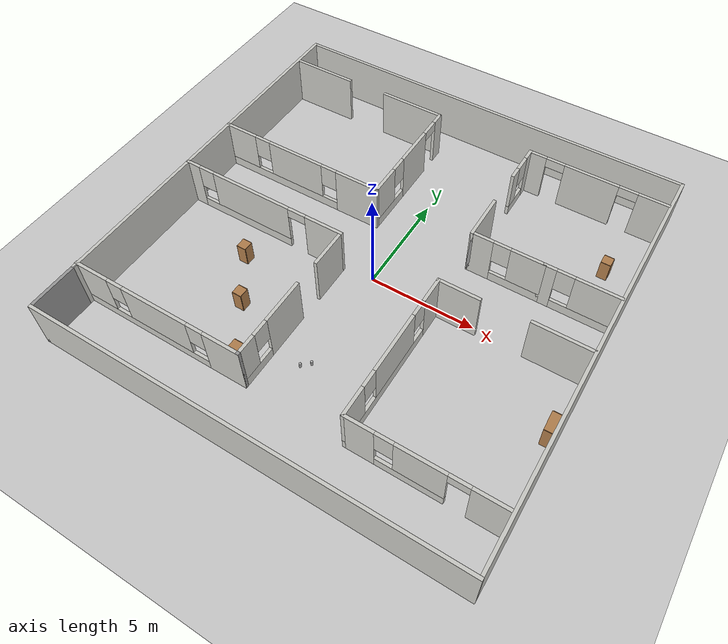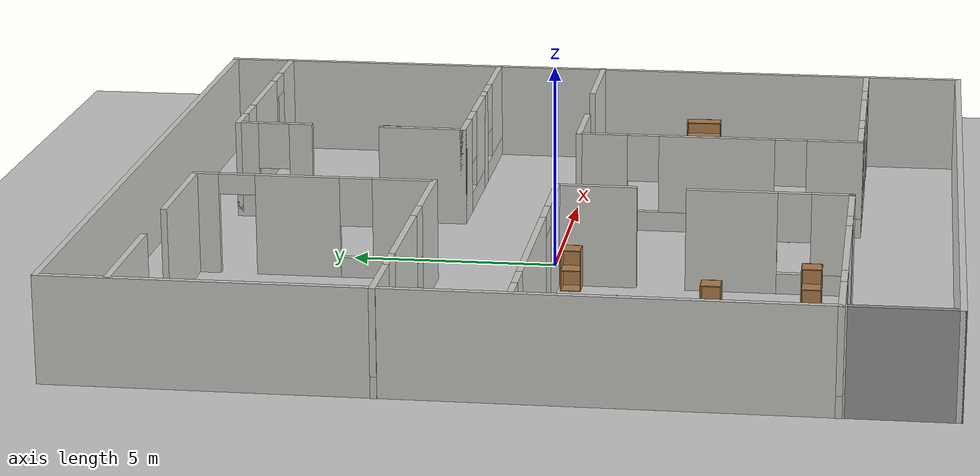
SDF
<sdf version="1.7">
 <world name="default">
  <light name="sun" type="directional">
   <pose>0 0 10 0 -0 0</pose>
   <diffuse>0.8 0.8 0.8 1</diffuse>
   <specular>0.2 0.2 0.2 1</specular>
   <attenuation>
    <range>1000</range>
    <constant>0.9</constant>
    <linear>0.01</linear>
    <quadratic>0.001</quadratic>
   </attenuation>
   <direction>-0.5 0.1 -0.9</direction>
   <spot><inner_angle>0</inner_angle><outer_angle>0</outer_angle><falloff>0</falloff></spot>
  </light>
  <model name="ground_plane">
   <static>1</static>
   <link name="link">
    <collision name="collision">
     <geometry><plane><normal>0 0 1</normal><size>100 100</size></plane></geometry>
     <surface>
      <contact><collide_bitmask>65535</collide_bitmask></contact>
      <friction><ode><mu>100</mu><mu2>50</mu2></ode></friction>
     </surface>
    </collision>
    <visual name="visual">
     <cast_shadows>0</cast_shadows>
     <geometry><plane><normal>0 0 1</normal><size>100 100</size></plane></geometry>
     <material>
      <script><uri>file://media/materials/scripts/gazebo.material</uri><name>Gazebo/Grey</name></script>
     </material>
    </visual>
   </link>
  </model>
  <gravity>0 0 -9.8</gravity>
  <magnetic_field>6e-06 2.3e-05 -4.2e-05</magnetic_field>
  <atmosphere type="adiabatic"/>
  <physics type="ode">
   <max_step_size>0.001</max_step_size>
   <real_time_factor>1</real_time_factor>
   <real_time_update_rate>1000</real_time_update_rate>
  </physics>
  <scene><ambient>0.4 0.4 0.4 1</ambient><background>0.7 0.7 0.7 1</background><shadows>1</shadows></scene>
  <audio><device>default</device></audio>
  <spherical_coordinates>
   <surface_model>EARTH_WGS84</surface_model>
   <latitude_deg>0</latitude_deg>
   <longitude_deg>0</longitude_deg>
   <elevation>0</elevation>
   <heading_deg>0</heading_deg>
  </spherical_coordinates>
  <model name="supermap">
   <pose>0.084091 0.18801 0 0 -0 0</pose>
   <link name="Wall_13">
    <collision name="Wall_13_Collision">
     <geometry><box><size>3.1968 0.15 2.5</size></box></geometry>
     <pose>0 0 1.25 0 -0 0</pose>
    </collision>
    <visual name="Wall_13_Visual">
     <pose>0 0 1.25 0 -0 0</pose>
     <geometry><box><size>3.1968 0.15 2.5</size></box></geometry>
     <material>
      <script><uri>file://media/materials/scripts/gazebo.material</uri><name>Gazebo/CeilingTiled</name></script>
      <ambient>1 1 1 1</ambient>
     </material>
     <meta><layer>0</layer></meta>
    </visual>
    <pose>-3.13164 8.41571 0 0 -0 0</pose>
   </link>
   <link name="Wall_16">
    <pose>-1.58164 5.49071 0 0 -0 -1.5708</pose>
    <visual name="Wall_16_Visual_0">
     <pose>-2.66773 0 1.25 0 -0 0</pose>
     <geometry><box><size>0.664542 0.15 2.5</size></box></geometry>
     <material>
      <script><uri>file://media/materials/scripts/gazebo.material</uri><name>Gazebo/CeilingTiled</name></script>
      <ambient>1 1 1 1</ambient>
     </material>
     <meta><layer>0</layer></meta>
    </visual>
    <collision name="Wall_16_Collision_0">
     <geometry><box><size>0.664542 0.15 2.5</size></box></geometry>
     <pose>-2.66773 0 1.25 0 -0 0</pose>
    </collision>
    <visual name="Wall_16_Visual_1">
     <pose>-0.400539 0 1.25 0 -0 0</pose>
     <geometry><box><size>2.06984 0.15 2.5</size></box></geometry>
     <material>
      <script><uri>file://media/materials/scripts/gazebo.material</uri><name>Gazebo/CeilingTiled</name></script>
      <ambient>1 1 1 1</ambient>
     </material>
     <meta><layer>0</layer></meta>
    </visual>
    <collision name="Wall_16_Collision_1">
     <geometry><box><size>2.06984 0.15 2.5</size></box></geometry>
     <pose>-0.400539 0 1.25 0 -0 0</pose>
    </collision>
    <visual name="Wall_16_Visual_2">
     <pose>1.81719 0 0.25 0 -0 0</pose>
     <geometry><box><size>2.36562 0.15 0.5</size></box></geometry>
     <material>
      <script><uri>file://media/materials/scripts/gazebo.material</uri><name>Gazebo/CeilingTiled</name></script>
      <ambient>1 1 1 1</ambient>
     </material>
     <meta><layer>0</layer></meta>
    </visual>
    <collision name="Wall_16_Collision_2">
     <geometry><box><size>2.36562 0.15 0.5</size></box></geometry>
     <pose>1.81719 0 0.25 0 -0 0</pose>
    </collision>
    <visual name="Wall_16_Visual_3">
     <pose>2.21719 0 1.5 0 -0 0</pose>
     <geometry><box><size>1.56562 0.15 2</size></box></geometry>
     <material>
      <script><uri>file://media/materials/scripts/gazebo.material</uri><name>Gazebo/CeilingTiled</name></script>
      <ambient>1 1 1 1</ambient>
     </material>
     <meta><layer>0</layer></meta>
    </visual>
    <collision name="Wall_16_Collision_3">
     <geometry><box><size>1.56562 0.15 2</size></box></geometry>
     <pose>2.21719 0 1.5 0 -0 0</pose>
    </collision>
    <visual name="Wall_16_Visual_4">
     <pose>1.03438 0 1.9 0 -0 0</pose>
     <geometry><box><size>0.8 0.15 1.2</size></box></geometry>
     <material>
      <script><uri>file://media/materials/scripts/gazebo.material</uri><name>Gazebo/CeilingTiled</name></script>
      <ambient>1 1 1 1</ambient>
     </material>
     <meta><layer>0</layer></meta>
    </visual>
    <collision name="Wall_16_Collision_4">
     <geometry><box><size>0.8 0.15 1.2</size></box></geometry>
     <pose>1.03438 0 1.9 0 -0 0</pose>
    </collision>
    <visual name="Wall_16_Visual_5">
     <pose>-1.88546 0 2.25 0 -0 0</pose>
     <geometry><box><size>0.9 0.15 0.5</size></box></geometry>
     <material>
      <script><uri>file://media/materials/scripts/gazebo.material</uri><name>Gazebo/CeilingTiled</name></script>
      <ambient>1 1 1 1</ambient>
     </material>
     <meta><layer>0</layer></meta>
    </visual>
    <collision name="Wall_16_Collision_5">
     <geometry><box><size>0.9 0.15 0.5</size></box></geometry>
     <pose>-1.88546 0 2.25 0 -0 0</pose>
    </collision>
   </link>
   <link name="Wall_17">
    <collision name="Wall_17_Collision">
     <geometry><box><size>0.15 0.15 2.5</size></box></geometry>
     <pose>0 0 1.25 0 -0 0</pose>
    </collision>
    <visual name="Wall_17_Visual">
     <pose>0 0 1.25 0 -0 0</pose>
     <geometry><box><size>0.15 0.15 2.5</size></box></geometry>
     <material>
      <script><uri>file://media/materials/scripts/gazebo.material</uri><name>Gazebo/Grey</name></script>
      <ambient>1 1 1 1</ambient>
     </material>
     <meta><layer>0</layer></meta>
    </visual>
    <pose>-1.58164 2.56571 0 0 -0 0</pose>
   </link>
   <link name="Wall_2">
    <collision name="Wall_2_Collision">
     <geometry><box><size>17.75 0.15 2.5</size></box></geometry>
     <pose>0 0 1.25 0 -0 0</pose>
    </collision>
    <visual name="Wall_2_Visual">
     <pose>0 0 1.25 0 -0 0</pose>
     <geometry><box><size>17.75 0.15 2.5</size></box></geometry>
     <material>
      <script><uri>file://media/materials/scripts/gazebo.material</uri><name>Gazebo/CeilingTiled</name></script>
      <ambient>1 1 1 1</ambient>
     </material>
     <meta><layer>0</layer></meta>
    </visual>
    <pose>-9.91033 1.175 0 0 -0 1.5708</pose>
   </link>
   <link name="Wall_21">
    <pose>-5.75664 2.56571 0 0 -0 3.14159</pose>
    <visual name="Wall_21_Visual_0">
     <pose>-3.13363 0 1.25 0 -0 0</pose>
     <geometry><box><size>2.23275 0.15 2.5</size></box></geometry>
     <material>
      <script><uri>file://media/materials/scripts/gazebo.material</uri><name>Gazebo/CeilingTiled</name></script>
      <ambient>1 1 1 1</ambient>
     </material>
     <meta><layer>0</layer></meta>
    </visual>
    <collision name="Wall_21_Collision_0">
     <geometry><box><size>2.23275 0.15 2.5</size></box></geometry>
     <pose>-3.13363 0 1.25 0 -0 0</pose>
    </collision>
    <visual name="Wall_21_Visual_1">
     <pose>1.11637 0 0.25 0 -0 0</pose>
     <geometry><box><size>6.26725 0.15 0.5</size></box></geometry>
     <material>
      <script><uri>file://media/materials/scripts/gazebo.material</uri><name>Gazebo/CeilingTiled</name></script>
      <ambient>1 1 1 1</ambient>
     </material>
     <meta><layer>0</layer></meta>
    </visual>
    <collision name="Wall_21_Collision_1">
     <geometry><box><size>6.26725 0.15 0.5</size></box></geometry>
     <pose>1.11637 0 0.25 0 -0 0</pose>
    </collision>
    <visual name="Wall_21_Visual_2">
     <pose>0.247221 0 1.5 0 -0 0</pose>
     <geometry><box><size>2.92895 0.15 2</size></box></geometry>
     <material>
      <script><uri>file://media/materials/scripts/gazebo.material</uri><name>Gazebo/CeilingTiled</name></script>
      <ambient>1 1 1 1</ambient>
     </material>
     <meta><layer>0</layer></meta>
    </visual>
    <collision name="Wall_21_Collision_2">
     <geometry><box><size>2.92895 0.15 2</size></box></geometry>
     <pose>0.247221 0 1.5 0 -0 0</pose>
    </collision>
    <visual name="Wall_21_Visual_3">
     <pose>3.38085 0 1.5 0 -0 0</pose>
     <geometry><box><size>1.7383 0.15 2</size></box></geometry>
     <material>
      <script><uri>file://media/materials/scripts/gazebo.material</uri><name>Gazebo/CeilingTiled</name></script>
      <ambient>1 1 1 1</ambient>
     </material>
     <meta><layer>0</layer></meta>
    </visual>
    <collision name="Wall_21_Collision_3">
     <geometry><box><size>1.7383 0.15 2</size></box></geometry>
     <pose>3.38085 0 1.5 0 -0 0</pose>
    </collision>
    <visual name="Wall_21_Visual_4">
     <pose>-1.61725 0 1.9 0 -0 0</pose>
     <geometry><box><size>0.8 0.15 1.2</size></box></geometry>
     <material>
      <script><uri>file://media/materials/scripts/gazebo.material</uri><name>Gazebo/CeilingTiled</name></script>
      <ambient>1 1 1 1</ambient>
     </material>
     <meta><layer>0</layer></meta>
    </visual>
    <collision name="Wall_21_Collision_4">
     <geometry><box><size>0.8 0.15 1.2</size></box></geometry>
     <pose>-1.61725 0 1.9 0 -0 0</pose>
    </collision>
    <visual name="Wall_21_Visual_5">
     <pose>2.1117 0 1.9 0 -0 0</pose>
     <geometry><box><size>0.8 0.15 1.2</size></box></geometry>
     <material>
      <script><uri>file://media/materials/scripts/gazebo.material</uri><name>Gazebo/CeilingTiled</name></script>
      <ambient>1 1 1 1</ambient>
     </material>
     <meta><layer>0</layer></meta>
    </visual>
    <collision name="Wall_21_Collision_5">
     <geometry><box><size>0.8 0.15 1.2</size></box></geometry>
     <pose>2.1117 0 1.9 0 -0 0</pose>
    </collision>
   </link>
   <link name="Wall_23">
    <pose>-5.72483 -0.405977 0 0 -0 0</pose>
    <visual name="Wall_23_Visual_0">
     <pose>-3.87306 0 1.25 0 -0 0</pose>
     <geometry><box><size>0.753885 0.15 2.5</size></box></geometry>
     <material>
      <script><uri>file://media/materials/scripts/gazebo.material</uri><name>Gazebo/CeilingTiled</name></script>
      <ambient>1 1 1 1</ambient>
     </material>
     <meta><layer>0</layer></meta>
    </visual>
    <collision name="Wall_23_Collision_0">
     <geometry><box><size>0.753885 0.15 2.5</size></box></geometry>
     <pose>-3.87306 0 1.25 0 -0 0</pose>
    </collision>
    <visual name="Wall_23_Visual_1">
     <pose>3.29505 0 1.25 0 -0 0</pose>
     <geometry><box><size>1.90991 0.15 2.5</size></box></geometry>
     <material>
      <script><uri>file://media/materials/scripts/gazebo.material</uri><name>Gazebo/CeilingTiled</name></script>
      <ambient>1 1 1 1</ambient>
     </material>
     <meta><layer>0</layer></meta>
    </visual>
    <collision name="Wall_23_Collision_1">
     <geometry><box><size>1.90991 0.15 2.5</size></box></geometry>
     <pose>3.29505 0 1.25 0 -0 0</pose>
    </collision>
    <visual name="Wall_23_Visual_2">
     <pose>-1.02801 0 0.25 0 -0 0</pose>
     <geometry><box><size>4.93621 0.15 0.5</size></box></geometry>
     <material>
      <script><uri>file://media/materials/scripts/gazebo.material</uri><name>Gazebo/CeilingTiled</name></script>
      <ambient>1 1 1 1</ambient>
     </material>
     <meta><layer>0</layer></meta>
    </visual>
    <collision name="Wall_23_Collision_2">
     <geometry><box><size>4.93621 0.15 0.5</size></box></geometry>
     <pose>-1.02801 0 0.25 0 -0 0</pose>
    </collision>
    <visual name="Wall_23_Visual_3">
     <pose>-0.628012 0 1.5 0 -0 0</pose>
     <geometry><box><size>4.13621 0.15 2</size></box></geometry>
     <material>
      <script><uri>file://media/materials/scripts/gazebo.material</uri><name>Gazebo/CeilingTiled</name></script>
      <ambient>1 1 1 1</ambient>
     </material>
     <meta><layer>0</layer></meta>
    </visual>
    <collision name="Wall_23_Collision_3">
     <geometry><box><size>4.13621 0.15 2</size></box></geometry>
     <pose>-0.628012 0 1.5 0 -0 0</pose>
    </collision>
    <visual name="Wall_23_Visual_4">
     <pose>-3.09612 0 1.9 0 -0 0</pose>
     <geometry><box><size>0.8 0.15 1.2</size></box></geometry>
     <material>
      <script><uri>file://media/materials/scripts/gazebo.material</uri><name>Gazebo/CeilingTiled</name></script>
      <ambient>1 1 1 1</ambient>
     </material>
     <meta><layer>0</layer></meta>
    </visual>
    <collision name="Wall_23_Collision_4">
     <geometry><box><size>0.8 0.15 1.2</size></box></geometry>
     <pose>-3.09612 0 1.9 0 -0 0</pose>
    </collision>
    <visual name="Wall_23_Visual_5">
     <pose>1.89009 0 2.25 0 -0 0</pose>
     <geometry><box><size>0.9 0.15 0.5</size></box></geometry>
     <material>
      <script><uri>file://media/materials/scripts/gazebo.material</uri><name>Gazebo/CeilingTiled</name></script>
      <ambient>1 1 1 1</ambient>
     </material>
     <meta><layer>0</layer></meta>
    </visual>
    <collision name="Wall_23_Collision_5">
     <geometry><box><size>0.9 0.15 0.5</size></box></geometry>
     <pose>1.89009 0 2.25 0 -0 0</pose>
    </collision>
   </link>
   <link name="Wall_25">
    <collision name="Wall_25_Collision">
     <geometry><box><size>2 0.15 2.5</size></box></geometry>
     <pose>0 0 1.25 0 -0 0</pose>
    </collision>
    <visual name="Wall_25_Visual">
     <pose>0 0 1.25 0 -0 0</pose>
     <geometry><box><size>2 0.15 2.5</size></box></geometry>
     <material>
      <script><uri>file://media/materials/scripts/gazebo.material</uri><name>Gazebo/CeilingTiled</name></script>
      <ambient>1 1 1 1</ambient>
     </material>
     <meta><layer>0</layer></meta>
    </visual>
    <pose>-1.54983 -1.33098 0 0 -0 -1.5708</pose>
   </link>
   <link name="Wall_27">
    <pose>-1.58967 -5.50689 0 0 -0 -1.5708</pose>
    <visual name="Wall_27_Visual_0">
     <pose>-0.912701 0 1.25 0 -0 0</pose>
     <geometry><box><size>2.1746 0.15 2.5</size></box></geometry>
     <material>
      <script><uri>file://media/materials/scripts/gazebo.material</uri><name>Gazebo/CeilingTiled</name></script>
      <ambient>1 1 1 1</ambient>
     </material>
     <meta><layer>0</layer></meta>
    </visual>
    <collision name="Wall_27_Collision_0">
     <geometry><box><size>2.1746 0.15 2.5</size></box></geometry>
     <pose>-0.912701 0 1.25 0 -0 0</pose>
    </collision>
    <visual name="Wall_27_Visual_1">
     <pose>1.0873 0 0.25 0 -0 0</pose>
     <geometry><box><size>1.8254 0.15 0.5</size></box></geometry>
     <material>
      <script><uri>file://media/materials/scripts/gazebo.material</uri><name>Gazebo/CeilingTiled</name></script>
      <ambient>1 1 1 1</ambient>
     </material>
     <meta><layer>0</layer></meta>
    </visual>
    <collision name="Wall_27_Collision_1">
     <geometry><box><size>1.8254 0.15 0.5</size></box></geometry>
     <pose>1.0873 0 0.25 0 -0 0</pose>
    </collision>
    <visual name="Wall_27_Visual_2">
     <pose>1.4873 0 1.5 0 -0 0</pose>
     <geometry><box><size>1.0254 0.15 2</size></box></geometry>
     <material>
      <script><uri>file://media/materials/scripts/gazebo.material</uri><name>Gazebo/CeilingTiled</name></script>
      <ambient>1 1 1 1</ambient>
     </material>
     <meta><layer>0</layer></meta>
    </visual>
    <collision name="Wall_27_Collision_2">
     <geometry><box><size>1.0254 0.15 2</size></box></geometry>
     <pose>1.4873 0 1.5 0 -0 0</pose>
    </collision>
    <visual name="Wall_27_Visual_3">
     <pose>0.574599 0 1.9 0 -0 0</pose>
     <geometry><box><size>0.8 0.15 1.2</size></box></geometry>
     <material>
      <script><uri>file://media/materials/scripts/gazebo.material</uri><name>Gazebo/CeilingTiled</name></script>
      <ambient>1 1 1 1</ambient>
     </material>
     <meta><layer>0</layer></meta>
    </visual>
    <collision name="Wall_27_Collision_3">
     <geometry><box><size>0.8 0.15 1.2</size></box></geometry>
     <pose>0.574599 0 1.9 0 -0 0</pose>
    </collision>
   </link>
   <link name="Wall_28">
    <collision name="Wall_28_Collision">
     <geometry><box><size>0.15 0.15 2.5</size></box></geometry>
     <pose>0 0 1.25 0 -0 0</pose>
    </collision>
    <visual name="Wall_28_Visual">
     <pose>0 0 1.25 0 -0 0</pose>
     <geometry><box><size>0.15 0.15 2.5</size></box></geometry>
     <material>
      <script><uri>file://media/materials/scripts/gazebo.material</uri><name>Gazebo/Grey</name></script>
      <ambient>1 1 1 1</ambient>
     </material>
     <meta><layer>0</layer></meta>
    </visual>
    <pose>-1.58967 -7.43189 0 0 -0 0</pose>
   </link>
   <link name="Wall_31">
    <collision name="Wall_31_Collision">
     <geometry><box><size>2.5 0.15 2.5</size></box></geometry>
     <pose>0 0 1.25 0 -0 0</pose>
    </collision>
    <visual name="Wall_31_Visual">
     <pose>0 0 1.25 0 -0 0</pose>
     <geometry><box><size>2.5 0.15 2.5</size></box></geometry>
     <material>
      <script><uri>file://media/materials/scripts/gazebo.material</uri><name>Gazebo/Grey</name></script>
      <ambient>1 1 1 1</ambient>
     </material>
     <meta><layer>0</layer></meta>
    </visual>
    <pose>-9.91033 -8.8 0 0 -0 -1.5708</pose>
   </link>
   <link name="Wall_38">
    <pose>-5.76467 -7.43189 0 0 -0 3.14159</pose>
    <visual name="Wall_38_Visual_0">
     <pose>-3.34507 0 1.25 0 -0 0</pose>
     <geometry><box><size>1.80986 0.15 2.5</size></box></geometry>
     <material>
      <script><uri>file://media/materials/scripts/gazebo.material</uri><name>Gazebo/CeilingTiled</name></script>
      <ambient>1 1 1 1</ambient>
     </material>
     <meta><layer>0</layer></meta>
    </visual>
    <collision name="Wall_38_Collision_0">
     <geometry><box><size>1.80986 0.15 2.5</size></box></geometry>
     <pose>-3.34507 0 1.25 0 -0 0</pose>
    </collision>
    <visual name="Wall_38_Visual_1">
     <pose>0.904931 0 0.25 0 -0 0</pose>
     <geometry><box><size>6.69014 0.15 0.5</size></box></geometry>
     <material>
      <script><uri>file://media/materials/scripts/gazebo.material</uri><name>Gazebo/CeilingTiled</name></script>
      <ambient>1 1 1 1</ambient>
     </material>
     <meta><layer>0</layer></meta>
    </visual>
    <collision name="Wall_38_Collision_1">
     <geometry><box><size>6.69014 0.15 0.5</size></box></geometry>
     <pose>0.904931 0 0.25 0 -0 0</pose>
    </collision>
    <visual name="Wall_38_Visual_2">
     <pose>0.030177 0 1.5 0 -0 0</pose>
     <geometry><box><size>3.34063 0.15 2</size></box></geometry>
     <material>
      <script><uri>file://media/materials/scripts/gazebo.material</uri><name>Gazebo/CeilingTiled</name></script>
      <ambient>1 1 1 1</ambient>
     </material>
     <meta><layer>0</layer></meta>
    </visual>
    <collision name="Wall_38_Collision_2">
     <geometry><box><size>3.34063 0.15 2</size></box></geometry>
     <pose>0.030177 0 1.5 0 -0 0</pose>
    </collision>
    <visual name="Wall_38_Visual_3">
     <pose>3.37525 0 1.5 0 -0 0</pose>
     <geometry><box><size>1.74951 0.15 2</size></box></geometry>
     <material>
      <script><uri>file://media/materials/scripts/gazebo.material</uri><name>Gazebo/CeilingTiled</name></script>
      <ambient>1 1 1 1</ambient>
     </material>
     <meta><layer>0</layer></meta>
    </visual>
    <collision name="Wall_38_Collision_3">
     <geometry><box><size>1.74951 0.15 2</size></box></geometry>
     <pose>3.37525 0 1.5 0 -0 0</pose>
    </collision>
    <visual name="Wall_38_Visual_4">
     <pose>-2.04014 0 1.9 0 -0 0</pose>
     <geometry><box><size>0.8 0.15 1.2</size></box></geometry>
     <material>
      <script><uri>file://media/materials/scripts/gazebo.material</uri><name>Gazebo/CeilingTiled</name></script>
      <ambient>1 1 1 1</ambient>
     </material>
     <meta><layer>0</layer></meta>
    </visual>
    <collision name="Wall_38_Collision_4">
     <geometry><box><size>0.8 0.15 1.2</size></box></geometry>
     <pose>-2.04014 0 1.9 0 -0 0</pose>
    </collision>
    <visual name="Wall_38_Visual_5">
     <pose>2.10049 0 1.9 0 -0 0</pose>
     <geometry><box><size>0.8 0.15 1.2</size></box></geometry>
     <material>
      <script><uri>file://media/materials/scripts/gazebo.material</uri><name>Gazebo/CeilingTiled</name></script>
      <ambient>1 1 1 1</ambient>
     </material>
     <meta><layer>0</layer></meta>
    </visual>
    <collision name="Wall_38_Collision_5">
     <geometry><box><size>0.8 0.15 1.2</size></box></geometry>
     <pose>2.10049 0 1.9 0 -0 0</pose>
    </collision>
   </link>
   <link name="Wall_40">
    <collision name="Wall_40_Collision">
     <geometry><box><size>20 0.15 2.5</size></box></geometry>
     <pose>0 0 1.25 0 -0 0</pose>
    </collision>
    <visual name="Wall_40_Visual">
     <pose>0 0 1.25 0 -0 0</pose>
     <geometry><box><size>20 0.15 2.5</size></box></geometry>
     <material>
      <script><uri>file://media/materials/scripts/gazebo.material</uri><name>Gazebo/CeilingTiled</name></script>
      <ambient>1 1 1 1</ambient>
     </material>
     <meta><layer>0</layer></meta>
    </visual>
    <pose>0.014666 -9.975 0 0 -0 0</pose>
   </link>
   <link name="Wall_47">
    <pose>3.22807 7.48394 0 0 -0 -1.5708</pose>
    <visual name="Wall_47_Visual_0">
     <pose>-0.700335 0 1.25 0 -0 0</pose>
     <geometry><box><size>0.59933 0.15 2.5</size></box></geometry>
     <material>
      <script><uri>file://media/materials/scripts/gazebo.material</uri><name>Gazebo/CeilingTiled</name></script>
      <ambient>1 1 1 1</ambient>
     </material>
     <meta><layer>0</layer></meta>
    </visual>
    <collision name="Wall_47_Collision_0">
     <geometry><box><size>0.59933 0.15 2.5</size></box></geometry>
     <pose>-0.700335 0 1.25 0 -0 0</pose>
    </collision>
    <visual name="Wall_47_Visual_1">
     <pose>0.299665 0 0.25 0 -0 0</pose>
     <geometry><box><size>1.40067 0.15 0.5</size></box></geometry>
     <material>
      <script><uri>file://media/materials/scripts/gazebo.material</uri><name>Gazebo/CeilingTiled</name></script>
      <ambient>1 1 1 1</ambient>
     </material>
     <meta><layer>0</layer></meta>
    </visual>
    <collision name="Wall_47_Collision_1">
     <geometry><box><size>1.40067 0.15 0.5</size></box></geometry>
     <pose>0.299665 0 0.25 0 -0 0</pose>
    </collision>
    <visual name="Wall_47_Visual_2">
     <pose>0.699665 0 1.5 0 -0 0</pose>
     <geometry><box><size>0.60067 0.15 2</size></box></geometry>
     <material>
      <script><uri>file://media/materials/scripts/gazebo.material</uri><name>Gazebo/CeilingTiled</name></script>
      <ambient>1 1 1 1</ambient>
     </material>
     <meta><layer>0</layer></meta>
    </visual>
    <collision name="Wall_47_Collision_2">
     <geometry><box><size>0.60067 0.15 2</size></box></geometry>
     <pose>0.699665 0 1.5 0 -0 0</pose>
    </collision>
    <visual name="Wall_47_Visual_3">
     <pose>-0.00067 0 1.9 0 -0 0</pose>
     <geometry><box><size>0.8 0.15 1.2</size></box></geometry>
     <material>
      <script><uri>file://media/materials/scripts/gazebo.material</uri><name>Gazebo/CeilingTiled</name></script>
      <ambient>1 1 1 1</ambient>
     </material>
     <meta><layer>0</layer></meta>
    </visual>
    <collision name="Wall_47_Collision_3">
     <geometry><box><size>0.8 0.15 1.2</size></box></geometry>
     <pose>-0.00067 0 1.9 0 -0 0</pose>
    </collision>
   </link>
   <link name="Wall_49">
    <collision name="Wall_49_Collision">
     <geometry><box><size>2.25 0.15 2.5</size></box></geometry>
     <pose>0 0 1.25 0 -0 0</pose>
    </collision>
    <visual name="Wall_49_Visual">
     <pose>0 0 1.25 0 -0 0</pose>
     <geometry><box><size>2.25 0.15 2.5</size></box></geometry>
     <material>
      <script><uri>file://media/materials/scripts/gazebo.material</uri><name>Gazebo/CeilingTiled</name></script>
      <ambient>1 1 1 1</ambient>
     </material>
     <meta><layer>0</layer></meta>
    </visual>
    <pose>3.19748 3.61897 0 0 -0 -1.5708</pose>
   </link>
   <link name="Wall_50">
    <collision name="Wall_50_Collision">
     <geometry><box><size>0.16 0.15 2.5</size></box></geometry>
     <pose>0 0 1.25 0 -0 0</pose>
    </collision>
    <visual name="Wall_50_Visual">
     <pose>0 0 1.25 0 -0 0</pose>
     <geometry><box><size>0.16 0.15 2.5</size></box></geometry>
     <material>
      <script><uri>file://media/materials/scripts/gazebo.material</uri><name>Gazebo/Grey</name></script>
      <ambient>1 1 1 1</ambient>
     </material>
     <meta><layer>0</layer></meta>
    </visual>
    <pose>3.20248 2.56897 0 0 -0 0</pose>
   </link>
   <link name="Wall_54">
    <pose>4.87248 2.56897 0 0 -0 0</pose>
    <visual name="Wall_54_Visual_0">
     <pose>-1.19885 0 1.25 0 -0 0</pose>
     <geometry><box><size>1.1023 0.15 2.5</size></box></geometry>
     <material>
      <script><uri>file://media/materials/scripts/gazebo.material</uri><name>Gazebo/CeilingTiled</name></script>
      <ambient>1 1 1 1</ambient>
     </material>
     <meta><layer>0</layer></meta>
    </visual>
    <collision name="Wall_54_Collision_0">
     <geometry><box><size>1.1023 0.15 2.5</size></box></geometry>
     <pose>-1.19885 0 1.25 0 -0 0</pose>
    </collision>
    <visual name="Wall_54_Visual_1">
     <pose>0.551148 0 0.25 0 -0 0</pose>
     <geometry><box><size>2.39771 0.15 0.5</size></box></geometry>
     <material>
      <script><uri>file://media/materials/scripts/gazebo.material</uri><name>Gazebo/CeilingTiled</name></script>
      <ambient>1 1 1 1</ambient>
     </material>
     <meta><layer>0</layer></meta>
    </visual>
    <collision name="Wall_54_Collision_1">
     <geometry><box><size>2.39771 0.15 0.5</size></box></geometry>
     <pose>0.551148 0 0.25 0 -0 0</pose>
    </collision>
    <visual name="Wall_54_Visual_2">
     <pose>0.951148 0 1.5 0 -0 0</pose>
     <geometry><box><size>1.5977 0.15 2</size></box></geometry>
     <material>
      <script><uri>file://media/materials/scripts/gazebo.material</uri><name>Gazebo/CeilingTiled</name></script>
      <ambient>1 1 1 1</ambient>
     </material>
     <meta><layer>0</layer></meta>
    </visual>
    <collision name="Wall_54_Collision_2">
     <geometry><box><size>1.5977 0.15 2</size></box></geometry>
     <pose>0.951148 0 1.5 0 -0 0</pose>
    </collision>
    <visual name="Wall_54_Visual_3">
     <pose>-0.247705 0 1.9 0 -0 0</pose>
     <geometry><box><size>0.8 0.15 1.2</size></box></geometry>
     <material>
      <script><uri>file://media/materials/scripts/gazebo.material</uri><name>Gazebo/CeilingTiled</name></script>
      <ambient>1 1 1 1</ambient>
     </material>
     <meta><layer>0</layer></meta>
    </visual>
    <collision name="Wall_54_Collision_3">
     <geometry><box><size>0.8 0.15 1.2</size></box></geometry>
     <pose>-0.247705 0 1.9 0 -0 0</pose>
    </collision>
   </link>
   <link name="Wall_56">
    <pose>8.22248 2.56897 0 0 -0 0</pose>
    <visual name="Wall_56_Visual_0">
     <pose>-1.43611 0 1.25 0 -0 0</pose>
     <geometry><box><size>0.627776 0.15 2.5</size></box></geometry>
     <material>
      <script><uri>file://media/materials/scripts/gazebo.material</uri><name>Gazebo/CeilingTiled</name></script>
      <ambient>1 1 1 1</ambient>
     </material>
     <meta><layer>0</layer></meta>
    </visual>
    <collision name="Wall_56_Collision_0">
     <geometry><box><size>0.627776 0.15 2.5</size></box></geometry>
     <pose>-1.43611 0 1.25 0 -0 0</pose>
    </collision>
    <visual name="Wall_56_Visual_1">
     <pose>0.313888 0 0.25 0 -0 0</pose>
     <geometry><box><size>2.87222 0.15 0.5</size></box></geometry>
     <material>
      <script><uri>file://media/materials/scripts/gazebo.material</uri><name>Gazebo/CeilingTiled</name></script>
      <ambient>1 1 1 1</ambient>
     </material>
     <meta><layer>0</layer></meta>
    </visual>
    <collision name="Wall_56_Collision_1">
     <geometry><box><size>2.87222 0.15 0.5</size></box></geometry>
     <pose>0.313888 0 0.25 0 -0 0</pose>
    </collision>
    <visual name="Wall_56_Visual_2">
     <pose>0.713888 0 1.5 0 -0 0</pose>
     <geometry><box><size>2.07222 0.15 2</size></box></geometry>
     <material>
      <script><uri>file://media/materials/scripts/gazebo.material</uri><name>Gazebo/CeilingTiled</name></script>
      <ambient>1 1 1 1</ambient>
     </material>
     <meta><layer>0</layer></meta>
    </visual>
    <collision name="Wall_56_Collision_2">
     <geometry><box><size>2.07222 0.15 2</size></box></geometry>
     <pose>0.713888 0 1.5 0 -0 0</pose>
    </collision>
    <visual name="Wall_56_Visual_3">
     <pose>-0.722224 0 1.9 0 -0 0</pose>
     <geometry><box><size>0.8 0.15 1.2</size></box></geometry>
     <material>
      <script><uri>file://media/materials/scripts/gazebo.material</uri><name>Gazebo/CeilingTiled</name></script>
      <ambient>1 1 1 1</ambient>
     </material>
     <meta><layer>0</layer></meta>
    </visual>
    <collision name="Wall_56_Collision_3">
     <geometry><box><size>0.8 0.15 1.2</size></box></geometry>
     <pose>-0.722224 0 1.9 0 -0 0</pose>
    </collision>
   </link>
   <link name="Wall_60">
    <pose>6.52807 8.40893 0 0 -0 0</pose>
    <visual name="Wall_60_Visual_0">
     <pose>-2.91788 0 1.25 0 -0 0</pose>
     <geometry><box><size>0.914233 0.15 2.5</size></box></geometry>
     <material>
      <script><uri>file://media/materials/scripts/gazebo.material</uri><name>Gazebo/CeilingTiled</name></script>
      <ambient>1 1 1 1</ambient>
     </material>
     <meta><layer>0</layer></meta>
    </visual>
    <collision name="Wall_60_Collision_0">
     <geometry><box><size>0.914233 0.15 2.5</size></box></geometry>
     <pose>-2.91788 0 1.25 0 -0 0</pose>
    </collision>
    <visual name="Wall_60_Visual_1">
     <pose>-0.260886 0 1.25 0 -0 0</pose>
     <geometry><box><size>2.59976 0.15 2.5</size></box></geometry>
     <material>
      <script><uri>file://media/materials/scripts/gazebo.material</uri><name>Gazebo/CeilingTiled</name></script>
      <ambient>1 1 1 1</ambient>
     </material>
     <meta><layer>0</layer></meta>
    </visual>
    <collision name="Wall_60_Collision_1">
     <geometry><box><size>2.59976 0.15 2.5</size></box></geometry>
     <pose>-0.260886 0 1.25 0 -0 0</pose>
    </collision>
    <visual name="Wall_60_Visual_2">
     <pose>2.657 0 1.25 0 -0 0</pose>
     <geometry><box><size>1.43601 0.15 2.5</size></box></geometry>
     <material>
      <script><uri>file://media/materials/scripts/gazebo.material</uri><name>Gazebo/CeilingTiled</name></script>
      <ambient>1 1 1 1</ambient>
     </material>
     <meta><layer>0</layer></meta>
    </visual>
    <collision name="Wall_60_Collision_2">
     <geometry><box><size>1.43601 0.15 2.5</size></box></geometry>
     <pose>2.657 0 1.25 0 -0 0</pose>
    </collision>
    <visual name="Wall_60_Visual_3">
     <pose>-2.01077 0 2.25 0 -0 0</pose>
     <geometry><box><size>0.9 0.15 0.5</size></box></geometry>
     <material>
      <script><uri>file://media/materials/scripts/gazebo.material</uri><name>Gazebo/CeilingTiled</name></script>
      <ambient>1 1 1 1</ambient>
     </material>
     <meta><layer>0</layer></meta>
    </visual>
    <collision name="Wall_60_Collision_3">
     <geometry><box><size>0.9 0.15 0.5</size></box></geometry>
     <pose>-2.01077 0 2.25 0 -0 0</pose>
    </collision>
    <visual name="Wall_60_Visual_4">
     <pose>1.48899 0 2.25 0 -0 0</pose>
     <geometry><box><size>0.9 0.15 0.5</size></box></geometry>
     <material>
      <script><uri>file://media/materials/scripts/gazebo.material</uri><name>Gazebo/CeilingTiled</name></script>
      <ambient>1 1 1 1</ambient>
     </material>
     <meta><layer>0</layer></meta>
    </visual>
    <collision name="Wall_60_Collision_4">
     <geometry><box><size>0.9 0.15 0.5</size></box></geometry>
     <pose>1.48899 0 2.25 0 -0 0</pose>
    </collision>
   </link>
   <link name="Wall_67">
    <pose>3.19101 -3.95842 0 0 -0 -1.5708</pose>
    <visual name="Wall_67_Visual_0">
     <pose>-2.97082 0 1.25 0 -0 0</pose>
     <geometry><box><size>1.30836 0.15 2.5</size></box></geometry>
     <material>
      <script><uri>file://media/materials/scripts/gazebo.material</uri><name>Gazebo/CeilingTiled</name></script>
      <ambient>1 1 1 1</ambient>
     </material>
     <meta><layer>0</layer></meta>
    </visual>
    <collision name="Wall_67_Collision_0">
     <geometry><box><size>1.30836 0.15 2.5</size></box></geometry>
     <pose>-2.97082 0 1.25 0 -0 0</pose>
    </collision>
    <visual name="Wall_67_Visual_1">
     <pose>0.654182 0 0.25 0 -0 0</pose>
     <geometry><box><size>5.94164 0.15 0.5</size></box></geometry>
     <material>
      <script><uri>file://media/materials/scripts/gazebo.material</uri><name>Gazebo/CeilingTiled</name></script>
      <ambient>1 1 1 1</ambient>
     </material>
     <meta><layer>0</layer></meta>
    </visual>
    <collision name="Wall_67_Collision_1">
     <geometry><box><size>5.94164 0.15 0.5</size></box></geometry>
     <pose>0.654182 0 0.25 0 -0 0</pose>
    </collision>
    <visual name="Wall_67_Visual_2">
     <pose>-0.052162 0 1.5 0 -0 0</pose>
     <geometry><box><size>2.92895 0.15 2</size></box></geometry>
     <material>
      <script><uri>file://media/materials/scripts/gazebo.material</uri><name>Gazebo/CeilingTiled</name></script>
      <ambient>1 1 1 1</ambient>
     </material>
     <meta><layer>0</layer></meta>
    </visual>
    <collision name="Wall_67_Collision_2">
     <geometry><box><size>2.92895 0.15 2</size></box></geometry>
     <pose>-0.052162 0 1.5 0 -0 0</pose>
    </collision>
    <visual name="Wall_67_Visual_3">
     <pose>2.91866 0 1.5 0 -0 0</pose>
     <geometry><box><size>1.41269 0.15 2</size></box></geometry>
     <material>
      <script><uri>file://media/materials/scripts/gazebo.material</uri><name>Gazebo/CeilingTiled</name></script>
      <ambient>1 1 1 1</ambient>
     </material>
     <meta><layer>0</layer></meta>
    </visual>
    <collision name="Wall_67_Collision_3">
     <geometry><box><size>1.41269 0.15 2</size></box></geometry>
     <pose>2.91866 0 1.5 0 -0 0</pose>
    </collision>
    <visual name="Wall_67_Visual_4">
     <pose>-1.91664 0 1.9 0 -0 0</pose>
     <geometry><box><size>0.8 0.15 1.2</size></box></geometry>
     <material>
      <script><uri>file://media/materials/scripts/gazebo.material</uri><name>Gazebo/CeilingTiled</name></script>
      <ambient>1 1 1 1</ambient>
     </material>
     <meta><layer>0</layer></meta>
    </visual>
    <collision name="Wall_67_Collision_4">
     <geometry><box><size>0.8 0.15 1.2</size></box></geometry>
     <pose>-1.91664 0 1.9 0 -0 0</pose>
    </collision>
    <visual name="Wall_67_Visual_5">
     <pose>1.81231 0 1.9 0 -0 0</pose>
     <geometry><box><size>0.8 0.15 1.2</size></box></geometry>
     <material>
      <script><uri>file://media/materials/scripts/gazebo.material</uri><name>Gazebo/CeilingTiled</name></script>
      <ambient>1 1 1 1</ambient>
     </material>
     <meta><layer>0</layer></meta>
    </visual>
    <collision name="Wall_67_Collision_5">
     <geometry><box><size>0.8 0.15 1.2</size></box></geometry>
     <pose>1.81231 0 1.9 0 -0 0</pose>
    </collision>
   </link>
   <link name="Wall_70">
    <collision name="Wall_70_Collision">
     <geometry><box><size>2 0.15 2.5</size></box></geometry>
     <pose>0 0 1.25 0 -0 0</pose>
    </collision>
    <visual name="Wall_70_Visual">
     <pose>0 0 1.25 0 -0 0</pose>
     <geometry><box><size>2 0.15 2.5</size></box></geometry>
     <material>
      <script><uri>file://media/materials/scripts/gazebo.material</uri><name>Gazebo/CeilingTiled</name></script>
      <ambient>1 1 1 1</ambient>
     </material>
     <meta><layer>0</layer></meta>
    </visual>
    <pose>4.11601 -0.40842 0 0 -0 0</pose>
   </link>
   <link name="Wall_74">
    <collision name="Wall_74_Collision">
     <geometry><box><size>2.75 0.15 2.5</size></box></geometry>
     <pose>0 0 1.25 0 -0 0</pose>
    </collision>
    <visual name="Wall_74_Visual">
     <pose>0 0 1.25 0 -0 0</pose>
     <geometry><box><size>2.75 0.15 2.5</size></box></geometry>
     <material>
      <script><uri>file://media/materials/scripts/gazebo.material</uri><name>Gazebo/CeilingTiled</name></script>
      <ambient>1 1 1 1</ambient>
     </material>
     <meta><layer>0</layer></meta>
    </visual>
    <pose>8.59327 -0.308567 0 0 -0 0</pose>
   </link>
   <link name="Wall_76">
    <pose>6.49101 -7.50842 0 0 -0 0</pose>
    <visual name="Wall_76_Visual_0">
     <pose>-2.67648 0 1.25 0 -0 0</pose>
     <geometry><box><size>1.39704 0.15 2.5</size></box></geometry>
     <material>
      <script><uri>file://media/materials/scripts/gazebo.material</uri><name>Gazebo/CeilingTiled</name></script>
      <ambient>1 1 1 1</ambient>
     </material>
     <meta><layer>0</layer></meta>
    </visual>
    <collision name="Wall_76_Collision_0">
     <geometry><box><size>1.39704 0.15 2.5</size></box></geometry>
     <pose>-2.67648 0 1.25 0 -0 0</pose>
    </collision>
    <visual name="Wall_76_Visual_1">
     <pose>2.62263 0 1.25 0 -0 0</pose>
     <geometry><box><size>1.50474 0.15 2.5</size></box></geometry>
     <material>
      <script><uri>file://media/materials/scripts/gazebo.material</uri><name>Gazebo/CeilingTiled</name></script>
      <ambient>1 1 1 1</ambient>
     </material>
     <meta><layer>0</layer></meta>
    </visual>
    <collision name="Wall_76_Collision_1">
     <geometry><box><size>1.50474 0.15 2.5</size></box></geometry>
     <pose>2.62263 0 1.25 0 -0 0</pose>
    </collision>
    <visual name="Wall_76_Visual_2">
     <pose>-0.50385 0 0.25 0 -0 0</pose>
     <geometry><box><size>2.94823 0.15 0.5</size></box></geometry>
     <material>
      <script><uri>file://media/materials/scripts/gazebo.material</uri><name>Gazebo/CeilingTiled</name></script>
      <ambient>1 1 1 1</ambient>
     </material>
     <meta><layer>0</layer></meta>
    </visual>
    <collision name="Wall_76_Collision_2">
     <geometry><box><size>2.94823 0.15 0.5</size></box></geometry>
     <pose>-0.50385 0 0.25 0 -0 0</pose>
    </collision>
    <visual name="Wall_76_Visual_3">
     <pose>-0.10385 0 1.5 0 -0 0</pose>
     <geometry><box><size>2.14823 0.15 2</size></box></geometry>
     <material>
      <script><uri>file://media/materials/scripts/gazebo.material</uri><name>Gazebo/CeilingTiled</name></script>
      <ambient>1 1 1 1</ambient>
     </material>
     <meta><layer>0</layer></meta>
    </visual>
    <collision name="Wall_76_Collision_3">
     <geometry><box><size>2.14823 0.15 2</size></box></geometry>
     <pose>-0.10385 0 1.5 0 -0 0</pose>
    </collision>
    <visual name="Wall_76_Visual_4">
     <pose>-1.57796 0 1.9 0 -0 0</pose>
     <geometry><box><size>0.8 0.15 1.2</size></box></geometry>
     <material>
      <script><uri>file://media/materials/scripts/gazebo.material</uri><name>Gazebo/CeilingTiled</name></script>
      <ambient>1 1 1 1</ambient>
     </material>
     <meta><layer>0</layer></meta>
    </visual>
    <collision name="Wall_76_Collision_4">
     <geometry><box><size>0.8 0.15 1.2</size></box></geometry>
     <pose>-1.57796 0 1.9 0 -0 0</pose>
    </collision>
    <visual name="Wall_76_Visual_5">
     <pose>1.42026 0 2.25 0 -0 0</pose>
     <geometry><box><size>0.9 0.15 0.5</size></box></geometry>
     <material>
      <script><uri>file://media/materials/scripts/gazebo.material</uri><name>Gazebo/CeilingTiled</name></script>
      <ambient>1 1 1 1</ambient>
     </material>
     <meta><layer>0</layer></meta>
    </visual>
    <collision name="Wall_76_Collision_5">
     <geometry><box><size>0.9 0.15 0.5</size></box></geometry>
     <pose>1.42026 0 2.25 0 -0 0</pose>
    </collision>
   </link>
   <link name="Wall_78">
    <collision name="Wall_78_Collision">
     <geometry><box><size>20 0.15 2.5</size></box></geometry>
     <pose>0 0 1.25 0 -0 0</pose>
    </collision>
    <visual name="Wall_78_Visual">
     <pose>0 0 1.25 0 -0 0</pose>
     <geometry><box><size>20 0.15 2.5</size></box></geometry>
     <material>
      <script><uri>file://media/materials/scripts/gazebo.material</uri><name>Gazebo/CeilingTiled</name></script>
      <ambient>1 1 1 1</ambient>
     </material>
     <meta><layer>0</layer></meta>
    </visual>
    <pose>0.014666 9.975 0 0 -0 0</pose>
   </link>
   <link name="Wall_8">
    <collision name="Wall_8_Collision">
     <geometry><box><size>3.25 0.15 2.5</size></box></geometry>
     <pose>0 0 1.25 0 -0 0</pose>
    </collision>
    <visual name="Wall_8_Visual">
     <pose>0 0 1.25 0 -0 0</pose>
     <geometry><box><size>3.25 0.15 2.5</size></box></geometry>
     <material>
      <script><uri>file://media/materials/scripts/gazebo.material</uri><name>Gazebo/CeilingTiled</name></script>
      <ambient>1 1 1 1</ambient>
     </material>
     <meta><layer>0</layer></meta>
    </visual>
    <pose>-8.29935 8.38381 0 0 -0 0</pose>
   </link>
   <link name="Wall_80">
    <collision name="Wall_80_Collision">
     <geometry><box><size>20 0.15 2.5</size></box></geometry>
     <pose>0 0 1.25 0 -0 0</pose>
    </collision>
    <visual name="Wall_80_Visual">
     <pose>0 0 1.25 0 -0 0</pose>
     <geometry><box><size>20 0.15 2.5</size></box></geometry>
     <material>
      <script><uri>file://media/materials/scripts/gazebo.material</uri><name>Gazebo/CeilingTiled</name></script>
      <ambient>1 1 1 1</ambient>
     </material>
     <meta><layer>0</layer></meta>
    </visual>
    <pose>9.93967 0.049999 0 0 -0 -1.5708</pose>
   </link>
   <static>1</static>
  </model>
  <model name="bookshelf">
   <static>1</static>
   <link name="link">
    <inertial><mass>1</mass></inertial>
    <collision name="back">
     <pose>0 0.005 0.6 0 -0 0</pose>
     <geometry><box><size>0.9 0.01 1.2</size></box></geometry>
    </collision>
    <visual name="visual1">
     <pose>0 0.005 0.6 0 -0 0</pose>
     <geometry><box><size>0.9 0.01 1.2</size></box></geometry>
     <material>
      <script><uri>file://media/materials/scripts/gazebo.material</uri><name>Gazebo/Wood</name></script>
     </material>
    </visual>
    <collision name="left_side">
     <pose>0.45 -0.195 0.6 0 -0 0</pose>
     <geometry><box><size>0.02 0.4 1.2</size></box></geometry>
    </collision>
    <visual name="visual2">
     <pose>0.45 -0.195 0.6 0 -0 0</pose>
     <geometry><box><size>0.02 0.4 1.2</size></box></geometry>
     <material>
      <script><uri>file://media/materials/scripts/gazebo.material</uri><name>Gazebo/Wood</name></script>
     </material>
    </visual>
    <collision name="right_side">
     <pose>-0.45 -0.195 0.6 0 -0 0</pose>
     <geometry><box><size>0.02 0.4 1.2</size></box></geometry>
    </collision>
    <visual name="visual3">
     <pose>-0.45 -0.195 0.6 0 -0 0</pose>
     <geometry><box><size>0.02 0.4 1.2</size></box></geometry>
     <material>
      <script><uri>file://media/materials/scripts/gazebo.material</uri><name>Gazebo/Wood</name></script>
     </material>
    </visual>
    <collision name="bottom">
     <pose>0 -0.195 0.03 0 -0 0</pose>
     <geometry><box><size>0.88 0.4 0.06</size></box></geometry>
    </collision>
    <visual name="visual4">
     <pose>0 -0.195 0.03 0 -0 0</pose>
     <geometry><box><size>0.88 0.4 0.06</size></box></geometry>
     <material>
      <script><uri>file://media/materials/scripts/gazebo.material</uri><name>Gazebo/Wood</name></script>
     </material>
    </visual>
    <collision name="top">
     <pose>0 -0.195 1.19 0 -0 0</pose>
     <geometry><box><size>0.88 0.4 0.02</size></box></geometry>
    </collision>
    <visual name="visual5">
     <pose>0 -0.195 1.19 0 -0 0</pose>
     <geometry><box><size>0.88 0.4 0.02</size></box></geometry>
     <material>
      <script><uri>file://media/materials/scripts/gazebo.material</uri><name>Gazebo/Wood</name></script>
     </material>
    </visual>
    <collision name="low_shelf">
     <pose>0 -0.195 0.43 0 -0 0</pose>
     <geometry><box><size>0.88 0.4 0.02</size></box></geometry>
    </collision>
    <visual name="visual6">
     <pose>0 -0.195 0.43 0 -0 0</pose>
     <geometry><box><size>0.88 0.4 0.02</size></box></geometry>
     <material>
      <script><uri>file://media/materials/scripts/gazebo.material</uri><name>Gazebo/Wood</name></script>
     </material>
    </visual>
    <collision name="high_shelf">
     <pose>0 -0.195 0.8 0 -0 0</pose>
     <geometry><box><size>0.88 0.4 0.02</size></box></geometry>
    </collision>
    <visual name="visual7">
     <pose>0 -0.195 0.8 0 -0 0</pose>
     <geometry><box><size>0.88 0.4 0.02</size></box></geometry>
     <material>
      <script><uri>file://media/materials/scripts/gazebo.material</uri><name>Gazebo/Wood</name></script>
     </material>
    </visual>
   </link>
   <pose>3.73306 -7.1906 0 0 0 -3.14005</pose>
  </model>
  <model name="cabinet">
   <static>1</static>
   <link name="cabinet_bottom_plate">
    <inertial>
     <pose>0 0 -1 0 -0 0</pose>
     <inertia><ixx>2.05</ixx><ixy>0</ixy><ixz>0</ixz><iyy>2.05</iyy><iyz>0</iyz><izz>2.05</izz></inertia>
     <mass>25</mass>
    </inertial>
    <collision name="cabinet_bottom_plate_geom">
     <pose>0 0 0.01 0 -0 0</pose>
     <geometry><box><size>0.45 0.45 0.02</size></box></geometry>
    </collision>
    <visual name="cabinet_bottom_plate_geom_visual">
     <pose>0 0 0.01 0 -0 0</pose>
     <geometry><box><size>0.45 0.45 0.02</size></box></geometry>
     <material>
      <script><uri>file://media/materials/scripts/gazebo.material</uri><name>Gazebo/Wood</name></script>
     </material>
    </visual>
    <collision name="cabinet_bottom_plate_geom_cabinet_back_plate">
     <pose>0.235 0 0.51 0 -0 0</pose>
     <geometry><box><size>0.02 0.45 1.02</size></box></geometry>
    </collision>
    <visual name="cabinet_bottom_plate_geom_cabinet_back_plate_visual">
     <pose>0.235 0 0.51 0 -0 0</pose>
     <geometry><box><size>0.02 0.45 1.02</size></box></geometry>
     <material>
      <script><uri>file://media/materials/scripts/gazebo.material</uri><name>Gazebo/Wood</name></script>
     </material>
    </visual>
    <collision name="cabinet_bottom_plate_geom_cabinet_left_plate">
     <pose>0 0.235 0.51 0 -0 0</pose>
     <geometry><box><size>0.45 0.02 1.02</size></box></geometry>
    </collision>
    <visual name="cabinet_bottom_plate_geom_cabinet_left_plate_visual">
     <pose>0 0.235 0.51 0 -0 0</pose>
     <geometry><box><size>0.45 0.02 1.02</size></box></geometry>
     <material>
      <script><uri>file://media/materials/scripts/gazebo.material</uri><name>Gazebo/Wood</name></script>
     </material>
    </visual>
    <collision name="cabinet_bottom_plate_geom_cabinet_middle_plate">
     <pose>0 0 0.51 0 -0 0</pose>
     <geometry><box><size>0.45 0.45 0.02</size></box></geometry>
    </collision>
    <visual name="cabinet_bottom_plate_geom_cabinet_middle_plate_visual">
     <pose>0 0 0.51 0 -0 0</pose>
     <geometry><box><size>0.45 0.45 0.02</size></box></geometry>
     <material>
      <script><uri>file://media/materials/scripts/gazebo.material</uri><name>Gazebo/Wood</name></script>
     </material>
    </visual>
    <collision name="cabinet_bottom_plate_geom_cabinet_right_plate">
     <pose>0 -0.235 0.51 0 -0 0</pose>
     <geometry><box><size>0.45 0.02 1.02</size></box></geometry>
    </collision>
    <visual name="cabinet_bottom_plate_geom_cabinet_right_plate_visual">
     <pose>0 -0.235 0.51 0 -0 0</pose>
     <geometry><box><size>0.45 0.02 1.02</size></box></geometry>
     <material>
      <script><uri>file://media/materials/scripts/gazebo.material</uri><name>Gazebo/Wood</name></script>
     </material>
    </visual>
    <collision name="cabinet_bottom_plate_geom_cabinet_top_plate">
     <pose>0 0 1.01 0 -0 0</pose>
     <geometry><box><size>0.45 0.45 0.02</size></box></geometry>
    </collision>
    <visual name="cabinet_bottom_plate_geom_cabinet_top_plate_visual">
     <pose>0 0 1.01 0 -0 0</pose>
     <geometry><box><size>0.45 0.45 0.02</size></box></geometry>
     <material>
      <script><uri>file://media/materials/scripts/gazebo.material</uri><name>Gazebo/Wood</name></script>
     </material>
    </visual>
   </link>
   <pose>-2.55622 -6.37269 0 0 -0 0</pose>
  </model>
  <model name="beer">
   <link name="link">
    <pose>0 0 0.115 0 -0 0</pose>
    <inertial>
     <mass>0.39</mass>
     <inertia><ixx>0.00058</ixx><ixy>0</ixy><ixz>0</ixz><iyy>0.00058</iyy><iyz>0</iyz><izz>0.00019</izz></inertia>
    </inertial>
    <collision name="collision">
     <geometry><cylinder><radius>0.055</radius><length>0.23</length></cylinder></geometry>
    </collision>
    <visual name="visual">
     <geometry><cylinder><radius>0.055</radius><length>0.23</length></cylinder></geometry>
     <material>
      <script>
       <uri>model://beer/materials/scripts</uri>
       <uri>model://beer/materials/textures</uri>
       <name>Beer/Diffuse</name>
      </script>
     </material>
    </visual>
   </link>
   <pose>0.141922 -5.70802 0.77499 1e-06 -2.7e-05 0.003055</pose>
  </model>
  <model name="beer_clone">
   <link name="link">
    <pose>0 0 0.115 0 -0 0</pose>
    <inertial>
     <mass>0.39</mass>
     <inertia><ixx>0.00058</ixx><ixy>0</ixy><ixz>0</ixz><iyy>0.00058</iyy><iyz>0</iyz><izz>0.00019</izz></inertia>
    </inertial>
    <collision name="collision">
     <geometry><cylinder><radius>0.055</radius><length>0.23</length></cylinder></geometry>
    </collision>
    <visual name="visual">
     <geometry><cylinder><radius>0.055</radius><length>0.23</length></cylinder></geometry>
     <material>
      <script>
       <uri>model://beer/materials/scripts</uri>
       <uri>model://beer/materials/textures</uri>
       <name>Beer/Diffuse</name>
      </script>
     </material>
    </visual>
   </link>
   <pose>0.476429 -5.38693 0.774992 -1e-06 2.7e-05 0.007628</pose>
  </model>
  <model name="cabinet_clone">
   <static>1</static>
   <link name="cabinet_bottom_plate">
    <inertial>
     <pose>0 0 -1 0 -0 0</pose>
     <inertia><ixx>2.05</ixx><ixy>0</ixy><ixz>0</ixz><iyy>2.05</iyy><iyz>0</iyz><izz>2.05</izz></inertia>
     <mass>25</mass>
    </inertial>
    <collision name="cabinet_bottom_plate_geom">
     <pose>0 0 0.01 0 -0 0</pose>
     <geometry><box><size>0.45 0.45 0.02</size></box></geometry>
    </collision>
    <visual name="cabinet_bottom_plate_geom_visual">
     <pose>0 0 0.01 0 -0 0</pose>
     <geometry><box><size>0.45 0.45 0.02</size></box></geometry>
     <material>
      <script><uri>file://media/materials/scripts/gazebo.material</uri><name>Gazebo/Wood</name></script>
     </material>
    </visual>
    <collision name="cabinet_bottom_plate_geom_cabinet_back_plate">
     <pose>0.235 0 0.51 0 -0 0</pose>
     <geometry><box><size>0.02 0.45 1.02</size></box></geometry>
    </collision>
    <visual name="cabinet_bottom_plate_geom_cabinet_back_plate_visual">
     <pose>0.235 0 0.51 0 -0 0</pose>
     <geometry><box><size>0.02 0.45 1.02</size></box></geometry>
     <material>
      <script><uri>file://media/materials/scripts/gazebo.material</uri><name>Gazebo/Wood</name></script>
     </material>
    </visual>
    <collision name="cabinet_bottom_plate_geom_cabinet_left_plate">
     <pose>0 0.235 0.51 0 -0 0</pose>
     <geometry><box><size>0.45 0.02 1.02</size></box></geometry>
    </collision>
    <visual name="cabinet_bottom_plate_geom_cabinet_left_plate_visual">
     <pose>0 0.235 0.51 0 -0 0</pose>
     <geometry><box><size>0.45 0.02 1.02</size></box></geometry>
     <material>
      <script><uri>file://media/materials/scripts/gazebo.material</uri><name>Gazebo/Wood</name></script>
     </material>
    </visual>
    <collision name="cabinet_bottom_plate_geom_cabinet_middle_plate">
     <pose>0 0 0.51 0 -0 0</pose>
     <geometry><box><size>0.45 0.45 0.02</size></box></geometry>
    </collision>
    <visual name="cabinet_bottom_plate_geom_cabinet_middle_plate_visual">
     <pose>0 0 0.51 0 -0 0</pose>
     <geometry><box><size>0.45 0.45 0.02</size></box></geometry>
     <material>
      <script><uri>file://media/materials/scripts/gazebo.material</uri><name>Gazebo/Wood</name></script>
     </material>
    </visual>
    <collision name="cabinet_bottom_plate_geom_cabinet_right_plate">
     <pose>0 -0.235 0.51 0 -0 0</pose>
     <geometry><box><size>0.45 0.02 1.02</size></box></geometry>
    </collision>
    <visual name="cabinet_bottom_plate_geom_cabinet_right_plate_visual">
     <pose>0 -0.235 0.51 0 -0 0</pose>
     <geometry><box><size>0.45 0.02 1.02</size></box></geometry>
     <material>
      <script><uri>file://media/materials/scripts/gazebo.material</uri><name>Gazebo/Wood</name></script>
     </material>
    </visual>
    <collision name="cabinet_bottom_plate_geom_cabinet_top_plate">
     <pose>0 0 1.01 0 -0 0</pose>
     <geometry><box><size>0.45 0.45 0.02</size></box></geometry>
    </collision>
    <visual name="cabinet_bottom_plate_geom_cabinet_top_plate_visual">
     <pose>0 0 1.01 0 -0 0</pose>
     <geometry><box><size>0.45 0.45 0.02</size></box></geometry>
     <material>
      <script><uri>file://media/materials/scripts/gazebo.material</uri><name>Gazebo/Wood</name></script>
     </material>
    </visual>
   </link>
   <pose>-1.78234 -0.607257 0 0 -0 0</pose>
  </model>
  <model name="cabinet_clone_0">
   <static>1</static>
   <link name="cabinet_bottom_plate">
    <inertial>
     <pose>0 0 -1 0 -0 0</pose>
     <inertia><ixx>2.05</ixx><ixy>0</ixy><ixz>0</ixz><iyy>2.05</iyy><iyz>0</iyz><izz>2.05</izz></inertia>
     <mass>25</mass>
    </inertial>
    <collision name="cabinet_bottom_plate_geom">
     <pose>0 0 0.01 0 -0 0</pose>
     <geometry><box><size>0.45 0.45 0.02</size></box></geometry>
    </collision>
    <visual name="cabinet_bottom_plate_geom_visual">
     <pose>0 0 0.01 0 -0 0</pose>
     <geometry><box><size>0.45 0.45 0.02</size></box></geometry>
     <material>
      <script><uri>file://media/materials/scripts/gazebo.material</uri><name>Gazebo/Wood</name></script>
     </material>
    </visual>
    <collision name="cabinet_bottom_plate_geom_cabinet_back_plate">
     <pose>0.235 0 0.51 0 -0 0</pose>
     <geometry><box><size>0.02 0.45 1.02</size></box></geometry>
    </collision>
    <visual name="cabinet_bottom_plate_geom_cabinet_back_plate_visual">
     <pose>0.235 0 0.51 0 -0 0</pose>
     <geometry><box><size>0.02 0.45 1.02</size></box></geometry>
     <material>
      <script><uri>file://media/materials/scripts/gazebo.material</uri><name>Gazebo/Wood</name></script>
     </material>
    </visual>
    <collision name="cabinet_bottom_plate_geom_cabinet_left_plate">
     <pose>0 0.235 0.51 0 -0 0</pose>
     <geometry><box><size>0.45 0.02 1.02</size></box></geometry>
    </collision>
    <visual name="cabinet_bottom_plate_geom_cabinet_left_plate_visual">
     <pose>0 0.235 0.51 0 -0 0</pose>
     <geometry><box><size>0.45 0.02 1.02</size></box></geometry>
     <material>
      <script><uri>file://media/materials/scripts/gazebo.material</uri><name>Gazebo/Wood</name></script>
     </material>
    </visual>
    <collision name="cabinet_bottom_plate_geom_cabinet_middle_plate">
     <pose>0 0 0.51 0 -0 0</pose>
     <geometry><box><size>0.45 0.45 0.02</size></box></geometry>
    </collision>
    <visual name="cabinet_bottom_plate_geom_cabinet_middle_plate_visual">
     <pose>0 0 0.51 0 -0 0</pose>
     <geometry><box><size>0.45 0.45 0.02</size></box></geometry>
     <material>
      <script><uri>file://media/materials/scripts/gazebo.material</uri><name>Gazebo/Wood</name></script>
     </material>
    </visual>
    <collision name="cabinet_bottom_plate_geom_cabinet_right_plate">
     <pose>0 -0.235 0.51 0 -0 0</pose>
     <geometry><box><size>0.45 0.02 1.02</size></box></geometry>
    </collision>
    <visual name="cabinet_bottom_plate_geom_cabinet_right_plate_visual">
     <pose>0 -0.235 0.51 0 -0 0</pose>
     <geometry><box><size>0.45 0.02 1.02</size></box></geometry>
     <material>
      <script><uri>file://media/materials/scripts/gazebo.material</uri><name>Gazebo/Wood</name></script>
     </material>
    </visual>
    <collision name="cabinet_bottom_plate_geom_cabinet_top_plate">
     <pose>0 0 1.01 0 -0 0</pose>
     <geometry><box><size>0.45 0.45 0.02</size></box></geometry>
    </collision>
    <visual name="cabinet_bottom_plate_geom_cabinet_top_plate_visual">
     <pose>0 0 1.01 0 -0 0</pose>
     <geometry><box><size>0.45 0.45 0.02</size></box></geometry>
     <material>
      <script><uri>file://media/materials/scripts/gazebo.material</uri><name>Gazebo/Wood</name></script>
     </material>
    </visual>
   </link>
   <pose>-5.50501 -1.96975 0 0 -0 0</pose>
  </model>
  <model name="cabinet_clone_1">
   <static>1</static>
   <link name="cabinet_bottom_plate">
    <inertial>
     <pose>0 0 -1 0 -0 0</pose>
     <inertia><ixx>2.05</ixx><ixy>0</ixy><ixz>0</ixz><iyy>2.05</iyy><iyz>0</iyz><izz>2.05</izz></inertia>
     <mass>25</mass>
    </inertial>
    <collision name="cabinet_bottom_plate_geom">
     <pose>0 0 0.01 0 -0 0</pose>
     <geometry><box><size>0.45 0.45 0.02</size></box></geometry>
    </collision>
    <visual name="cabinet_bottom_plate_geom_visual">
     <pose>0 0 0.01 0 -0 0</pose>
     <geometry><box><size>0.45 0.45 0.02</size></box></geometry>
     <material>
      <script><uri>file://media/materials/scripts/gazebo.material</uri><name>Gazebo/Wood</name></script>
     </material>
    </visual>
    <collision name="cabinet_bottom_plate_geom_cabinet_back_plate">
     <pose>0.235 0 0.51 0 -0 0</pose>
     <geometry><box><size>0.02 0.45 1.02</size></box></geometry>
    </collision>
    <visual name="cabinet_bottom_plate_geom_cabinet_back_plate_visual">
     <pose>0.235 0 0.51 0 -0 0</pose>
     <geometry><box><size>0.02 0.45 1.02</size></box></geometry>
     <material>
      <script><uri>file://media/materials/scripts/gazebo.material</uri><name>Gazebo/Wood</name></script>
     </material>
    </visual>
    <collision name="cabinet_bottom_plate_geom_cabinet_left_plate">
     <pose>0 0.235 0.51 0 -0 0</pose>
     <geometry><box><size>0.45 0.02 1.02</size></box></geometry>
    </collision>
    <visual name="cabinet_bottom_plate_geom_cabinet_left_plate_visual">
     <pose>0 0.235 0.51 0 -0 0</pose>
     <geometry><box><size>0.45 0.02 1.02</size></box></geometry>
     <material>
      <script><uri>file://media/materials/scripts/gazebo.material</uri><name>Gazebo/Wood</name></script>
     </material>
    </visual>
    <collision name="cabinet_bottom_plate_geom_cabinet_middle_plate">
     <pose>0 0 0.51 0 -0 0</pose>
     <geometry><box><size>0.45 0.45 0.02</size></box></geometry>
    </collision>
    <visual name="cabinet_bottom_plate_geom_cabinet_middle_plate_visual">
     <pose>0 0 0.51 0 -0 0</pose>
     <geometry><box><size>0.45 0.45 0.02</size></box></geometry>
     <material>
      <script><uri>file://media/materials/scripts/gazebo.material</uri><name>Gazebo/Wood</name></script>
     </material>
    </visual>
    <collision name="cabinet_bottom_plate_geom_cabinet_right_plate">
     <pose>0 -0.235 0.51 0 -0 0</pose>
     <geometry><box><size>0.45 0.02 1.02</size></box></geometry>
    </collision>
    <visual name="cabinet_bottom_plate_geom_cabinet_right_plate_visual">
     <pose>0 -0.235 0.51 0 -0 0</pose>
     <geometry><box><size>0.45 0.02 1.02</size></box></geometry>
     <material>
      <script><uri>file://media/materials/scripts/gazebo.material</uri><name>Gazebo/Wood</name></script>
     </material>
    </visual>
    <collision name="cabinet_bottom_plate_geom_cabinet_top_plate">
     <pose>0 0 1.01 0 -0 0</pose>
     <geometry><box><size>0.45 0.45 0.02</size></box></geometry>
    </collision>
    <visual name="cabinet_bottom_plate_geom_cabinet_top_plate_visual">
     <pose>0 0 1.01 0 -0 0</pose>
     <geometry><box><size>0.45 0.45 0.02</size></box></geometry>
     <material>
      <script><uri>file://media/materials/scripts/gazebo.material</uri><name>Gazebo/Wood</name></script>
     </material>
    </visual>
   </link>
   <pose>-4.09494 -4.11223 0 0 -0 0</pose>
  </model>
  <model name="cabinet_clone_1_clone">
   <static>1</static>
   <link name="cabinet_bottom_plate">
    <inertial>
     <pose>0 0 -1 0 -0 0</pose>
     <inertia><ixx>2.05</ixx><ixy>0</ixy><ixz>0</ixz><iyy>2.05</iyy><iyz>0</iyz><izz>2.05</izz></inertia>
     <mass>25</mass>
    </inertial>
    <collision name="cabinet_bottom_plate_geom">
     <pose>0 0 0.01 0 -0 0</pose>
     <geometry><box><size>0.45 0.45 0.02</size></box></geometry>
    </collision>
    <visual name="cabinet_bottom_plate_geom_visual">
     <pose>0 0 0.01 0 -0 0</pose>
     <geometry><box><size>0.45 0.45 0.02</size></box></geometry>
     <material>
      <script><uri>file://media/materials/scripts/gazebo.material</uri><name>Gazebo/Wood</name></script>
     </material>
    </visual>
    <collision name="cabinet_bottom_plate_geom_cabinet_back_plate">
     <pose>0.235 0 0.51 0 -0 0</pose>
     <geometry><box><size>0.02 0.45 1.02</size></box></geometry>
    </collision>
    <visual name="cabinet_bottom_plate_geom_cabinet_back_plate_visual">
     <pose>0.235 0 0.51 0 -0 0</pose>
     <geometry><box><size>0.02 0.45 1.02</size></box></geometry>
     <material>
      <script><uri>file://media/materials/scripts/gazebo.material</uri><name>Gazebo/Wood</name></script>
     </material>
    </visual>
    <collision name="cabinet_bottom_plate_geom_cabinet_left_plate">
     <pose>0 0.235 0.51 0 -0 0</pose>
     <geometry><box><size>0.45 0.02 1.02</size></box></geometry>
    </collision>
    <visual name="cabinet_bottom_plate_geom_cabinet_left_plate_visual">
     <pose>0 0.235 0.51 0 -0 0</pose>
     <geometry><box><size>0.45 0.02 1.02</size></box></geometry>
     <material>
      <script><uri>file://media/materials/scripts/gazebo.material</uri><name>Gazebo/Wood</name></script>
     </material>
    </visual>
    <collision name="cabinet_bottom_plate_geom_cabinet_middle_plate">
     <pose>0 0 0.51 0 -0 0</pose>
     <geometry><box><size>0.45 0.45 0.02</size></box></geometry>
    </collision>
    <visual name="cabinet_bottom_plate_geom_cabinet_middle_plate_visual">
     <pose>0 0 0.51 0 -0 0</pose>
     <geometry><box><size>0.45 0.45 0.02</size></box></geometry>
     <material>
      <script><uri>file://media/materials/scripts/gazebo.material</uri><name>Gazebo/Wood</name></script>
     </material>
    </visual>
    <collision name="cabinet_bottom_plate_geom_cabinet_right_plate">
     <pose>0 -0.235 0.51 0 -0 0</pose>
     <geometry><box><size>0.45 0.02 1.02</size></box></geometry>
    </collision>
    <visual name="cabinet_bottom_plate_geom_cabinet_right_plate_visual">
     <pose>0 -0.235 0.51 0 -0 0</pose>
     <geometry><box><size>0.45 0.02 1.02</size></box></geometry>
     <material>
      <script><uri>file://media/materials/scripts/gazebo.material</uri><name>Gazebo/Wood</name></script>
     </material>
    </visual>
    <collision name="cabinet_bottom_plate_geom_cabinet_top_plate">
     <pose>0 0 1.01 0 -0 0</pose>
     <geometry><box><size>0.45 0.45 0.02</size></box></geometry>
    </collision>
    <visual name="cabinet_bottom_plate_geom_cabinet_top_plate_visual">
     <pose>0 0 1.01 0 -0 0</pose>
     <geometry><box><size>0.45 0.45 0.02</size></box></geometry>
     <material>
      <script><uri>file://media/materials/scripts/gazebo.material</uri><name>Gazebo/Wood</name></script>
     </material>
    </visual>
   </link>
   <pose>8.60509 5.5987 0 0 -0 0</pose>
  </model>
  <model name="bookshelf_0">
   <static>1</static>
   <link name="link">
    <inertial><mass>1</mass></inertial>
    <collision name="back">
     <pose>0 0.005 0.6 0 -0 0</pose>
     <geometry><box><size>0.9 0.01 1.2</size></box></geometry>
    </collision>
    <visual name="visual1">
     <pose>0 0.005 0.6 0 -0 0</pose>
     <geometry><box><size>0.9 0.01 1.2</size></box></geometry>
     <material>
      <script><uri>file://media/materials/scripts/gazebo.material</uri><name>Gazebo/Wood</name></script>
     </material>
    </visual>
    <collision name="left_side">
     <pose>0.45 -0.195 0.6 0 -0 0</pose>
     <geometry><box><size>0.02 0.4 1.2</size></box></geometry>
    </collision>
    <visual name="visual2">
     <pose>0.45 -0.195 0.6 0 -0 0</pose>
     <geometry><box><size>0.02 0.4 1.2</size></box></geometry>
     <material>
      <script><uri>file://media/materials/scripts/gazebo.material</uri><name>Gazebo/Wood</name></script>
     </material>
    </visual>
    <collision name="right_side">
     <pose>-0.45 -0.195 0.6 0 -0 0</pose>
     <geometry><box><size>0.02 0.4 1.2</size></box></geometry>
    </collision>
    <visual name="visual3">
     <pose>-0.45 -0.195 0.6 0 -0 0</pose>
     <geometry><box><size>0.02 0.4 1.2</size></box></geometry>
     <material>
      <script><uri>file://media/materials/scripts/gazebo.material</uri><name>Gazebo/Wood</name></script>
     </material>
    </visual>
    <collision name="bottom">
     <pose>0 -0.195 0.03 0 -0 0</pose>
     <geometry><box><size>0.88 0.4 0.06</size></box></geometry>
    </collision>
    <visual name="visual4">
     <pose>0 -0.195 0.03 0 -0 0</pose>
     <geometry><box><size>0.88 0.4 0.06</size></box></geometry>
     <material>
      <script><uri>file://media/materials/scripts/gazebo.material</uri><name>Gazebo/Wood</name></script>
     </material>
    </visual>
    <collision name="top">
     <pose>0 -0.195 1.19 0 -0 0</pose>
     <geometry><box><size>0.88 0.4 0.02</size></box></geometry>
    </collision>
    <visual name="visual5">
     <pose>0 -0.195 1.19 0 -0 0</pose>
     <geometry><box><size>0.88 0.4 0.02</size></box></geometry>
     <material>
      <script><uri>file://media/materials/scripts/gazebo.material</uri><name>Gazebo/Wood</name></script>
     </material>
    </visual>
    <collision name="low_shelf">
     <pose>0 -0.195 0.43 0 -0 0</pose>
     <geometry><box><size>0.88 0.4 0.02</size></box></geometry>
    </collision>
    <visual name="visual6">
     <pose>0 -0.195 0.43 0 -0 0</pose>
     <geometry><box><size>0.88 0.4 0.02</size></box></geometry>
     <material>
      <script><uri>file://media/materials/scripts/gazebo.material</uri><name>Gazebo/Wood</name></script>
     </material>
    </visual>
    <collision name="high_shelf">
     <pose>0 -0.195 0.8 0 -0 0</pose>
     <geometry><box><size>0.88 0.4 0.02</size></box></geometry>
    </collision>
    <visual name="visual7">
     <pose>0 -0.195 0.8 0 -0 0</pose>
     <geometry><box><size>0.88 0.4 0.02</size></box></geometry>
     <material>
      <script><uri>file://media/materials/scripts/gazebo.material</uri><name>Gazebo/Wood</name></script>
     </material>
    </visual>
   </link>
   <pose>9.9044 -2.93801 0 0 0 -1.54157</pose>
  </model>
 </world>
</sdf>
